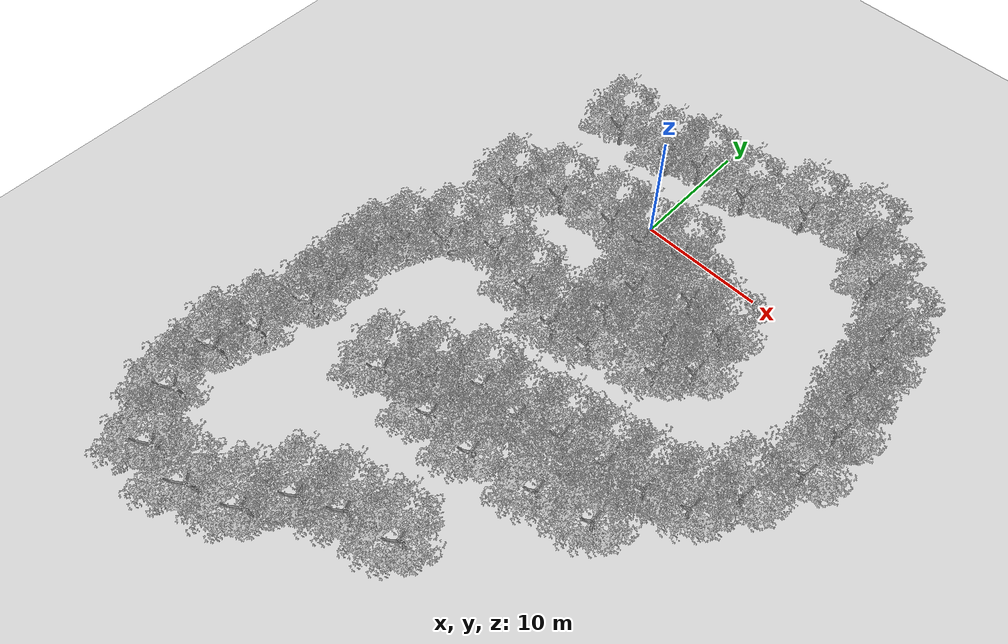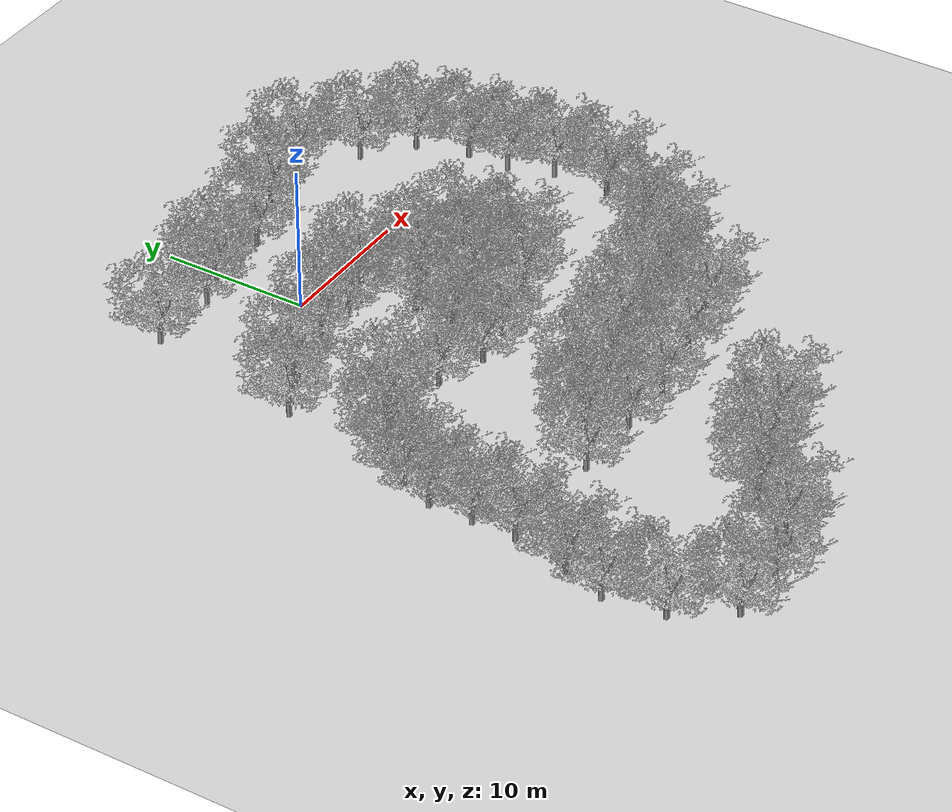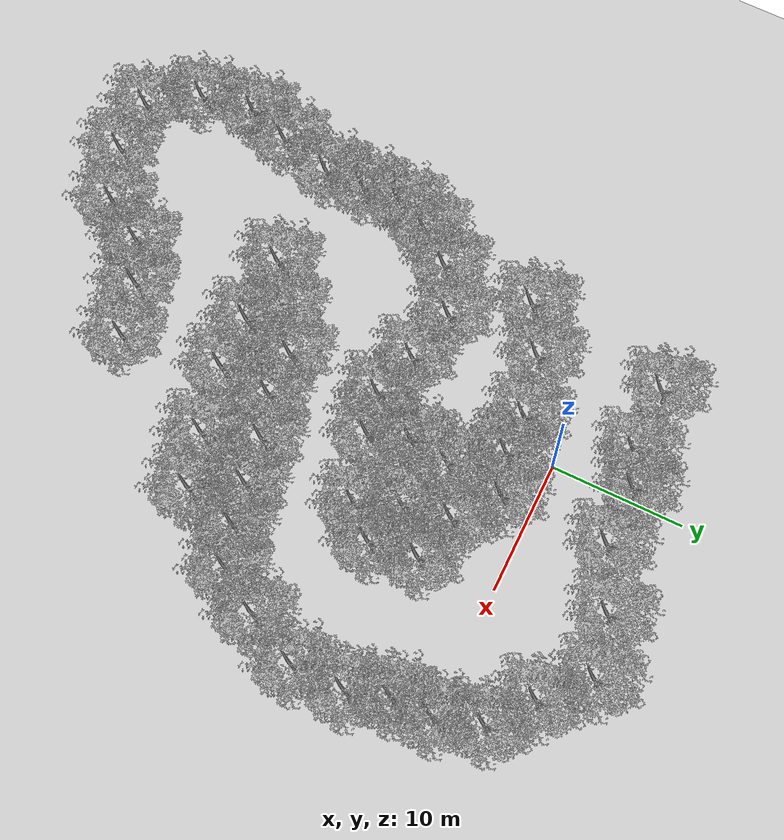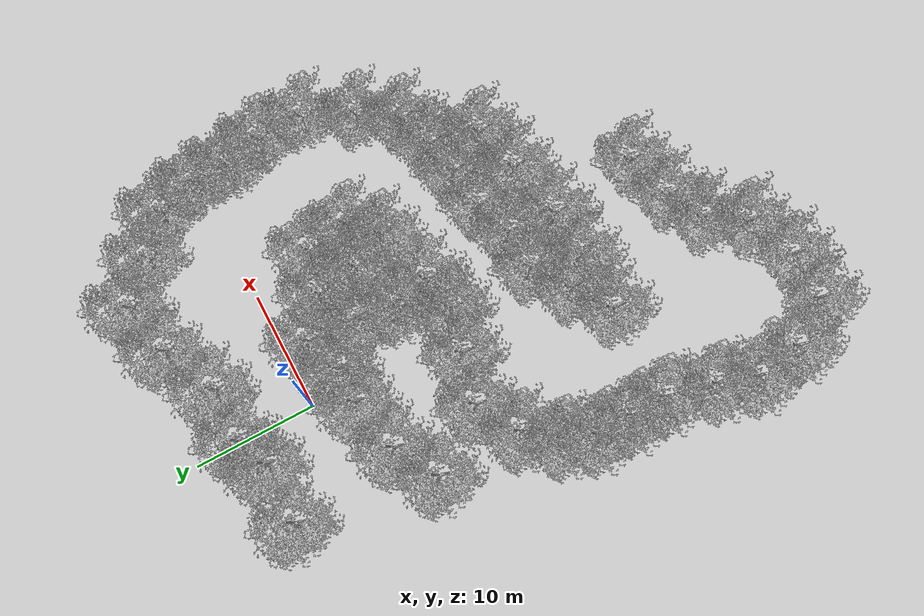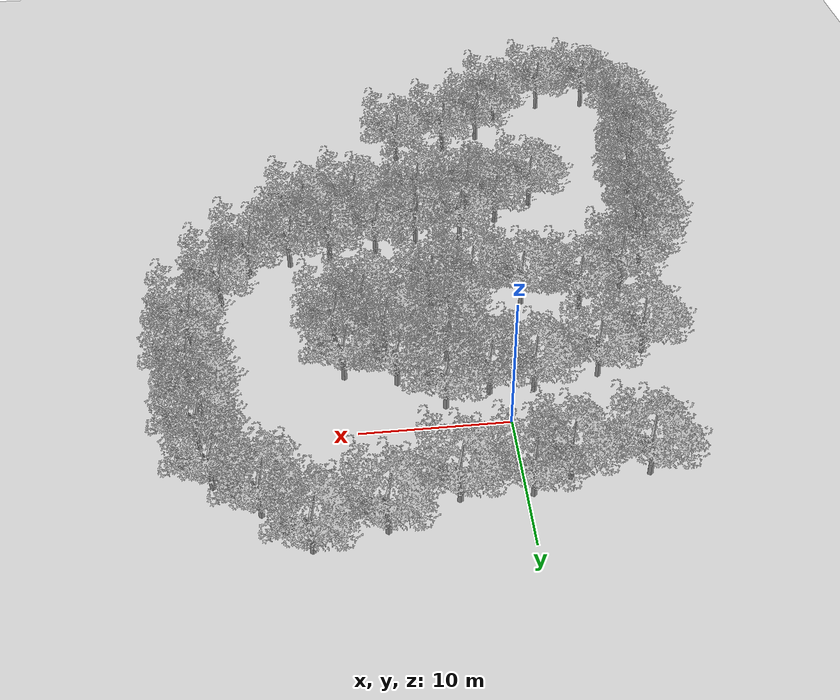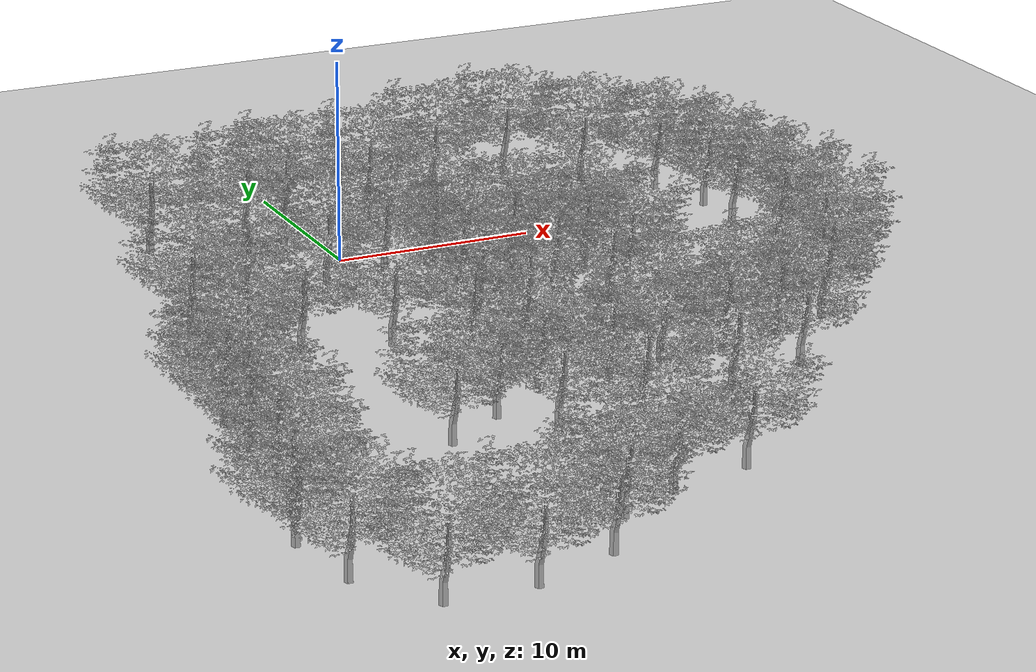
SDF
<?xml version="1.0" ?>
<gazebo version="1.2">
	<world name="default">

		<scene>
			<grid>false</grid>
		</scene>

    	<!-- A global light source -->
		<include>
			<uri>model://sun</uri>
		</include>

    	<!-- A ground plane -->
		<include>
			<uri>model://ground_plane</uri>
		</include>

		<model name='finihed'>
			<pose>8.508060 8.000000 0.000000 0.000000 -0.000000 0.000000</pose>
			<static>1</static>
			<allow_auto_disable>1</allow_auto_disable>
			<link name='link'>
				<pose>0.000000 0.000000 0.000000 0.000000 -0.000000 0.000000</pose>
				<inertial>
					<mass>10.000000</mass>
					<pose>0.000000 0.000000 0.000000 0.000000 -0.000000 0.000000</pose>
					<inertia>
						<ixx>0.001000</ixx>
						<ixy>0.000000</ixy>
						<ixz>0.000000</ixz>
						<iyy>0.001000</iyy>
						<iyz>0.000000</iyz>
						<izz>0.001000</izz>
					</inertia>
				</inertial>
				<collision name='collision'>
					<geometry>
						<cylinder>
							<radius>0.150000</radius>
							<length>5.000000</length>
						</cylinder>
					</geometry>
					<surface>
						<bounce />
						<friction>
							<ode />
						</friction>
						<contact>
							<ode />
						</contact>
					</surface>
				</collision>
				<visual name='visual'>
					<geometry>
						<mesh>
							<uri>model://finihed/meshes/finihed.dae</uri>
							<scale>1.000000 1.000000 1.000000</scale>
						</mesh>
					</geometry>
				</visual>
				<velocity_decay>
					<linear>0.000000</linear>
					<angular>0.000000</angular>
				</velocity_decay>
				<self_collide>0</self_collide>
				<kinematic>0</kinematic>
			</link>
		</model>

		<model name='finihed_0'>
			<pose>-0.515080 6.000000 0.000000 0.000000 -0.000000 0.000000</pose>
			<static>1</static>
			<allow_auto_disable>1</allow_auto_disable>
			<link name='link'>
				<pose>0.000000 0.000000 0.000000 0.000000 -0.000000 0.000000</pose>
				<inertial>
					<mass>10.000000</mass>
					<pose>0.000000 0.000000 0.000000 0.000000 -0.000000 0.000000</pose>
					<inertia>
						<ixx>0.001000</ixx>
						<ixy>0.000000</ixy>
						<ixz>0.000000</ixz>
						<iyy>0.001000</iyy>
						<iyz>0.000000</iyz>
						<izz>0.001000</izz>
					</inertia>
				</inertial>
				<collision name='collision'>
					<geometry>
						<cylinder>
							<radius>0.150000</radius>
							<length>5.000000</length>
						</cylinder>
					</geometry>
					<surface>
						<bounce />
						<friction>
							<ode />
						</friction>
						<contact>
							<ode />
						</contact>
					</surface>
				</collision>
				<visual name='visual'>
					<geometry>
						<mesh>
							<uri>model://finihed/meshes/finihed.dae</uri>
							<scale>1.000000 1.000000 1.000000</scale>
						</mesh>
					</geometry>
				</visual>
				<velocity_decay>
					<linear>0.000000</linear>
					<angular>0.000000</angular>
				</velocity_decay>
				<self_collide>0</self_collide>
				<kinematic>0</kinematic>
			</link>
		</model>
		<model name='finihed_1'>
			<pose>20.000000 0.000000 0.000000 0.000000 -0.000000 0.000000</pose>
			<static>1</static>
			<allow_auto_disable>1</allow_auto_disable>
			<link name='link'>
				<pose>0.000000 0.000000 0.000000 0.000000 -0.000000 0.000000</pose>
				<inertial>
					<mass>10.000000</mass>
					<pose>0.000000 0.000000 0.000000 0.000000 -0.000000 0.000000</pose>
					<inertia>
						<ixx>0.001000</ixx>
						<ixy>0.000000</ixy>
						<ixz>0.000000</ixz>
						<iyy>0.001000</iyy>
						<iyz>0.000000</iyz>
						<izz>0.001000</izz>
					</inertia>
				</inertial>
				<collision name='collision'>
					<geometry>
						<cylinder>
							<radius>0.150000</radius>
							<length>5.000000</length>
						</cylinder>
					</geometry>
					<surface>
						<bounce />
						<friction>
							<ode />
						</friction>
						<contact>
							<ode />
						</contact>
					</surface>
				</collision>
				<visual name='visual'>
					<geometry>
						<mesh>
							<uri>model://finihed/meshes/finihed.dae</uri>
							<scale>1.000000 1.000000 1.000000</scale>
						</mesh>
					</geometry>
				</visual>
				<velocity_decay>
					<linear>0.000000</linear>
					<angular>0.000000</angular>
				</velocity_decay>
				<self_collide>0</self_collide>
				<kinematic>0</kinematic>
			</link>
		</model>
		<model name='finihed_2'>
			<pose>16.000000 6.000000 0.000000 0.000000 -0.000000 0.000000</pose>
			<static>1</static>
			<allow_auto_disable>1</allow_auto_disable>
			<link name='link'>
				<pose>0.000000 0.000000 0.000000 0.000000 -0.000000 0.000000</pose>
				<inertial>
					<mass>10.000000</mass>
					<pose>0.000000 0.000000 0.000000 0.000000 -0.000000 0.000000</pose>
					<inertia>
						<ixx>0.001000</ixx>
						<ixy>0.000000</ixy>
						<ixz>0.000000</ixz>
						<iyy>0.001000</iyy>
						<iyz>0.000000</iyz>
						<izz>0.001000</izz>
					</inertia>
				</inertial>
				<collision name='collision'>
					<geometry>
						<cylinder>
							<radius>0.150000</radius>
							<length>5.000000</length>
						</cylinder>
					</geometry>
					<surface>
						<bounce />
						<friction>
							<ode />
						</friction>
						<contact>
							<ode />
						</contact>
					</surface>
				</collision>
				<visual name='visual'>
					<geometry>
						<mesh>
							<uri>model://finihed/meshes/finihed.dae</uri>
							<scale>1.000000 1.000000 1.000000</scale>
						</mesh>
					</geometry>
				</visual>
				<velocity_decay>
					<linear>0.000000</linear>
					<angular>0.000000</angular>
				</velocity_decay>
				<self_collide>0</self_collide>
				<kinematic>0</kinematic>
			</link>
		</model>
		<model name='finihed_3'>
			<pose>-8.000000 5.000000 0.000000 0.000000 -0.000000 0.000000</pose>
			<static>1</static>
			<allow_auto_disable>1</allow_auto_disable>
			<link name='link'>
				<pose>0.000000 0.000000 0.000000 0.000000 -0.000000 0.000000</pose>
				<inertial>
					<mass>10.000000</mass>
					<pose>0.000000 0.000000 0.000000 0.000000 -0.000000 0.000000</pose>
					<inertia>
						<ixx>0.001000</ixx>
						<ixy>0.000000</ixy>
						<ixz>0.000000</ixz>
						<iyy>0.001000</iyy>
						<iyz>0.000000</iyz>
						<izz>0.001000</izz>
					</inertia>
				</inertial>
				<collision name='collision'>
					<geometry>
						<cylinder>
							<radius>0.150000</radius>
							<length>5.000000</length>
						</cylinder>
					</geometry>
					<surface>
						<bounce />
						<friction>
							<ode />
						</friction>
						<contact>
							<ode />
						</contact>
					</surface>
				</collision>
				<visual name='visual'>
					<geometry>
						<mesh>
							<uri>model://finihed/meshes/finihed.dae</uri>
							<scale>1.000000 1.000000 1.000000</scale>
						</mesh>
					</geometry>
				</visual>
				<velocity_decay>
					<linear>0.000000</linear>
					<angular>0.000000</angular>
				</velocity_decay>
				<self_collide>0</self_collide>
				<kinematic>0</kinematic>
			</link>
		</model>
		<model name='finihed_4'>
			<pose>1.000000 -3.000000 0.000000 0.000000 -0.000000 0.000000</pose>
			<static>1</static>
			<allow_auto_disable>1</allow_auto_disable>
			<link name='link'>
				<pose>0.000000 0.000000 0.000000 0.000000 -0.000000 0.000000</pose>
				<inertial>
					<mass>10.000000</mass>
					<pose>0.000000 0.000000 0.000000 0.000000 -0.000000 0.000000</pose>
					<inertia>
						<ixx>0.001000</ixx>
						<ixy>0.000000</ixy>
						<ixz>0.000000</ixz>
						<iyy>0.001000</iyy>
						<iyz>0.000000</iyz>
						<izz>0.001000</izz>
					</inertia>
				</inertial>
				<collision name='collision'>
					<geometry>
						<cylinder>
							<radius>0.150000</radius>
							<length>5.000000</length>
						</cylinder>
					</geometry>
					<surface>
						<bounce />
						<friction>
							<ode />
						</friction>
						<contact>
							<ode />
						</contact>
					</surface>
				</collision>
				<visual name='visual'>
					<geometry>
						<mesh>
							<uri>model://finihed/meshes/finihed.dae</uri>
							<scale>1.000000 1.000000 1.000000</scale>
						</mesh>
					</geometry>
				</visual>
				<velocity_decay>
					<linear>0.000000</linear>
					<angular>0.000000</angular>
				</velocity_decay>
				<self_collide>0</self_collide>
				<kinematic>0</kinematic>
			</link>
		</model>
		<model name='finihed_5'>
			<pose>7.000000 -4.502550 0.000000 0.000000 -0.000000 0.000000</pose>
			<static>1</static>
			<allow_auto_disable>1</allow_auto_disable>
			<link name='link'>
				<pose>0.000000 0.000000 0.000000 0.000000 -0.000000 0.000000</pose>
				<inertial>
					<mass>10.000000</mass>
					<pose>0.000000 0.000000 0.000000 0.000000 -0.000000 0.000000</pose>
					<inertia>
						<ixx>0.001000</ixx>
						<ixy>0.000000</ixy>
						<ixz>0.000000</ixz>
						<iyy>0.001000</iyy>
						<iyz>0.000000</iyz>
						<izz>0.001000</izz>
					</inertia>
				</inertial>
				<collision name='collision'>
					<geometry>
						<cylinder>
							<radius>0.150000</radius>
							<length>5.000000</length>
						</cylinder>
					</geometry>
					<surface>
						<bounce />
						<friction>
							<ode />
						</friction>
						<contact>
							<ode />
						</contact>
					</surface>
				</collision>
				<visual name='visual'>
					<geometry>
						<mesh>
							<uri>model://finihed/meshes/finihed.dae</uri>
							<scale>1.000000 1.000000 1.000000</scale>
						</mesh>
					</geometry>
				</visual>
				<velocity_decay>
					<linear>0.000000</linear>
					<angular>0.000000</angular>
				</velocity_decay>
				<self_collide>0</self_collide>
				<kinematic>0</kinematic>
			</link>
		</model>
		<model name='finihed_6'>
			<pose>11.000000 -9.000000 0.000000 0.000000 -0.000000 0.000000</pose>
			<static>1</static>
			<allow_auto_disable>1</allow_auto_disable>
			<link name='link'>
				<pose>0.000000 0.000000 0.000000 0.000000 -0.000000 0.000000</pose>
				<inertial>
					<mass>10.000000</mass>
					<pose>0.000000 0.000000 0.000000 0.000000 -0.000000 0.000000</pose>
					<inertia>
						<ixx>0.001000</ixx>
						<ixy>0.000000</ixy>
						<ixz>0.000000</ixz>
						<iyy>0.001000</iyy>
						<iyz>0.000000</iyz>
						<izz>0.001000</izz>
					</inertia>
				</inertial>
				<collision name='collision'>
					<geometry>
						<cylinder>
							<radius>0.150000</radius>
							<length>5.000000</length>
						</cylinder>
					</geometry>
					<surface>
						<bounce />
						<friction>
							<ode />
						</friction>
						<contact>
							<ode />
						</contact>
					</surface>
				</collision>
				<visual name='visual'>
					<geometry>
						<mesh>
							<uri>model://finihed/meshes/finihed.dae</uri>
							<scale>1.000000 1.000000 1.000000</scale>
						</mesh>
					</geometry>
				</visual>
				<velocity_decay>
					<linear>0.000000</linear>
					<angular>0.000000</angular>
				</velocity_decay>
				<self_collide>0</self_collide>
				<kinematic>0</kinematic>
			</link>
		</model>
		<model name='finihed_7'>
			<pose>19.000000 3.502910 0.000000 0.000000 -0.000000 0.000000</pose>
			<static>1</static>
			<allow_auto_disable>1</allow_auto_disable>
			<link name='link'>
				<pose>0.000000 0.000000 0.000000 0.000000 -0.000000 0.000000</pose>
				<inertial>
					<mass>10.000000</mass>
					<pose>0.000000 0.000000 0.000000 0.000000 -0.000000 0.000000</pose>
					<inertia>
						<ixx>0.001000</ixx>
						<ixy>0.000000</ixy>
						<ixz>0.000000</ixz>
						<iyy>0.001000</iyy>
						<iyz>0.000000</iyz>
						<izz>0.001000</izz>
					</inertia>
				</inertial>
				<collision name='collision'>
					<geometry>
						<cylinder>
							<radius>0.150000</radius>
							<length>5.000000</length>
						</cylinder>
					</geometry>
					<surface>
						<bounce />
						<friction>
							<ode />
						</friction>
						<contact>
							<ode />
						</contact>
					</surface>
				</collision>
				<visual name='visual'>
					<geometry>
						<mesh>
							<uri>model://finihed/meshes/finihed.dae</uri>
							<scale>1.000000 1.000000 1.000000</scale>
						</mesh>
					</geometry>
				</visual>
				<velocity_decay>
					<linear>0.000000</linear>
					<angular>0.000000</angular>
				</velocity_decay>
				<self_collide>0</self_collide>
				<kinematic>0</kinematic>
			</link>
		</model>
		<model name='finihed_8'>
			<pose>13.000000 9.000000 0.000000 0.000000 -0.000000 0.000000</pose>
			<static>1</static>
			<allow_auto_disable>1</allow_auto_disable>
			<link name='link'>
				<pose>0.000000 0.000000 0.000000 0.000000 -0.000000 0.000000</pose>
				<inertial>
					<mass>10.000000</mass>
					<pose>0.000000 0.000000 0.000000 0.000000 -0.000000 0.000000</pose>
					<inertia>
						<ixx>0.001000</ixx>
						<ixy>0.000000</ixy>
						<ixz>0.000000</ixz>
						<iyy>0.001000</iyy>
						<iyz>0.000000</iyz>
						<izz>0.001000</izz>
					</inertia>
				</inertial>
				<collision name='collision'>
					<geometry>
						<cylinder>
							<radius>0.150000</radius>
							<length>5.000000</length>
						</cylinder>
					</geometry>
					<surface>
						<bounce />
						<friction>
							<ode />
						</friction>
						<contact>
							<ode />
						</contact>
					</surface>
				</collision>
				<visual name='visual'>
					<geometry>
						<mesh>
							<uri>model://finihed/meshes/finihed.dae</uri>
							<scale>1.000000 1.000000 1.000000</scale>
						</mesh>
					</geometry>
				</visual>
				<velocity_decay>
					<linear>0.000000</linear>
					<angular>0.000000</angular>
				</velocity_decay>
				<self_collide>0</self_collide>
				<kinematic>0</kinematic>
			</link>
		</model>
		<model name='finihed_9'>
			<pose>4.000000 6.000000 0.000000 0.000000 -0.000000 0.000000</pose>
			<static>1</static>
			<allow_auto_disable>1</allow_auto_disable>
			<link name='link'>
				<pose>0.000000 0.000000 0.000000 0.000000 -0.000000 0.000000</pose>
				<inertial>
					<mass>10.000000</mass>
					<pose>0.000000 0.000000 0.000000 0.000000 -0.000000 0.000000</pose>
					<inertia>
						<ixx>0.001000</ixx>
						<ixy>0.000000</ixy>
						<ixz>0.000000</ixz>
						<iyy>0.001000</iyy>
						<iyz>0.000000</iyz>
						<izz>0.001000</izz>
					</inertia>
				</inertial>
				<collision name='collision'>
					<geometry>
						<cylinder>
							<radius>0.150000</radius>
							<length>5.000000</length>
						</cylinder>
					</geometry>
					<surface>
						<bounce />
						<friction>
							<ode />
						</friction>
						<contact>
							<ode />
						</contact>
					</surface>
				</collision>
				<visual name='visual'>
					<geometry>
						<mesh>
							<uri>model://finihed/meshes/finihed.dae</uri>
							<scale>1.000000 1.000000 1.000000</scale>
						</mesh>
					</geometry>
				</visual>
				<velocity_decay>
					<linear>0.000000</linear>
					<angular>0.000000</angular>
				</velocity_decay>
				<self_collide>0</self_collide>
				<kinematic>0</kinematic>
			</link>
		</model>
		<model name='finihed_10'>
			<pose>4.000000 -2.000000 0.000000 0.000000 -0.000000 0.000000</pose>
			<static>1</static>
			<allow_auto_disable>1</allow_auto_disable>
			<link name='link'>
				<pose>0.000000 0.000000 0.000000 0.000000 -0.000000 0.000000</pose>
				<inertial>
					<mass>10.000000</mass>
					<pose>0.000000 0.000000 0.000000 0.000000 -0.000000 0.000000</pose>
					<inertia>
						<ixx>0.001000</ixx>
						<ixy>0.000000</ixy>
						<ixz>0.000000</ixz>
						<iyy>0.001000</iyy>
						<iyz>0.000000</iyz>
						<izz>0.001000</izz>
					</inertia>
				</inertial>
				<collision name='collision'>
					<geometry>
						<cylinder>
							<radius>0.150000</radius>
							<length>5.000000</length>
						</cylinder>
					</geometry>
					<surface>
						<bounce />
						<friction>
							<ode />
						</friction>
						<contact>
							<ode />
						</contact>
					</surface>
				</collision>
				<visual name='visual'>
					<geometry>
						<mesh>
							<uri>model://finihed/meshes/finihed.dae</uri>
							<scale>1.000000 1.000000 1.000000</scale>
						</mesh>
					</geometry>
				</visual>
				<velocity_decay>
					<linear>0.000000</linear>
					<angular>0.000000</angular>
				</velocity_decay>
				<self_collide>0</self_collide>
				<kinematic>0</kinematic>
			</link>
		</model>
		<model name='finihed_11'>
			<pose>10.517400 -5.416000 0.000000 0.000000 -0.000000 0.000000</pose>
			<static>1</static>
			<allow_auto_disable>1</allow_auto_disable>
			<link name='link'>
				<pose>0.000000 0.000000 0.000000 0.000000 -0.000000 0.000000</pose>
				<inertial>
					<mass>10.000000</mass>
					<pose>0.000000 0.000000 0.000000 0.000000 -0.000000 0.000000</pose>
					<inertia>
						<ixx>0.001000</ixx>
						<ixy>0.000000</ixy>
						<ixz>0.000000</ixz>
						<iyy>0.001000</iyy>
						<iyz>0.000000</iyz>
						<izz>0.001000</izz>
					</inertia>
				</inertial>
				<collision name='collision'>
					<geometry>
						<cylinder>
							<radius>0.150000</radius>
							<length>5.000000</length>
						</cylinder>
					</geometry>
					<surface>
						<bounce />
						<friction>
							<ode />
						</friction>
						<contact>
							<ode />
						</contact>
					</surface>
				</collision>
				<visual name='visual'>
					<geometry>
						<mesh>
							<uri>model://finihed/meshes/finihed.dae</uri>
							<scale>1.000000 1.000000 1.000000</scale>
						</mesh>
					</geometry>
				</visual>
				<velocity_decay>
					<linear>0.000000</linear>
					<angular>0.000000</angular>
				</velocity_decay>
				<self_collide>0</self_collide>
				<kinematic>0</kinematic>
			</link>
		</model>
		<model name='finihed_12'>
			<pose>20.000000 -3.000000 0.000000 0.000000 -0.000000 0.000000</pose>
			<static>1</static>
			<allow_auto_disable>1</allow_auto_disable>
			<link name='link'>
				<pose>0.000000 0.000000 0.000000 0.000000 -0.000000 0.000000</pose>
				<inertial>
					<mass>10.000000</mass>
					<pose>0.000000 0.000000 0.000000 0.000000 -0.000000 0.000000</pose>
					<inertia>
						<ixx>0.001000</ixx>
						<ixy>0.000000</ixy>
						<ixz>0.000000</ixz>
						<iyy>0.001000</iyy>
						<iyz>0.000000</iyz>
						<izz>0.001000</izz>
					</inertia>
				</inertial>
				<collision name='collision'>
					<geometry>
						<cylinder>
							<radius>0.150000</radius>
							<length>5.000000</length>
						</cylinder>
					</geometry>
					<surface>
						<bounce />
						<friction>
							<ode />
						</friction>
						<contact>
							<ode />
						</contact>
					</surface>
				</collision>
				<visual name='visual'>
					<geometry>
						<mesh>
							<uri>model://finihed/meshes/finihed.dae</uri>
							<scale>1.000000 1.000000 1.000000</scale>
						</mesh>
					</geometry>
				</visual>
				<velocity_decay>
					<linear>0.000000</linear>
					<angular>0.000000</angular>
				</velocity_decay>
				<self_collide>0</self_collide>
				<kinematic>0</kinematic>
			</link>
		</model>

		<model name='finihed_13'>
			<pose>21.000000 -6.000000 0.000000 0.000000 -0.000000 0.000000</pose>
			<static>1</static>
			<allow_auto_disable>1</allow_auto_disable>
			<link name='link'>
				<pose>0.000000 0.000000 0.000000 0.000000 -0.000000 0.000000</pose>
				<inertial>
					<mass>10.000000</mass>
					<pose>0.000000 0.000000 0.000000 0.000000 -0.000000 0.000000</pose>
					<inertia>
						<ixx>0.001000</ixx>
						<ixy>0.000000</ixy>
						<ixz>0.000000</ixz>
						<iyy>0.001000</iyy>
						<iyz>0.000000</iyz>
						<izz>0.001000</izz>
					</inertia>
				</inertial>
				<collision name='collision'>
					<geometry>
						<cylinder>
							<radius>0.150000</radius>
							<length>5.000000</length>
						</cylinder>
					</geometry>
					<surface>
						<bounce />
						<friction>
							<ode />
						</friction>
						<contact>
							<ode />
						</contact>
					</surface>
				</collision>
				<visual name='visual'>
					<geometry>
						<mesh>
							<uri>model://finihed/meshes/finihed.dae</uri>
							<scale>1.000000 1.000000 1.000000</scale>
						</mesh>
					</geometry>
				</visual>
				<velocity_decay>
					<linear>0.000000</linear>
					<angular>0.000000</angular>
				</velocity_decay>
				<self_collide>0</self_collide>
				<kinematic>0</kinematic>
			</link>
		</model>
		<model name='finihed_14'>
			<pose>21.000000 -10.000000 0.000000 0.000000 -0.000000 0.000000</pose>
			<static>1</static>
			<allow_auto_disable>1</allow_auto_disable>
			<link name='link'>
				<pose>0.000000 0.000000 0.000000 0.000000 -0.000000 0.000000</pose>
				<inertial>
					<mass>10.000000</mass>
					<pose>0.000000 0.000000 0.000000 0.000000 -0.000000 0.000000</pose>
					<inertia>
						<ixx>0.001000</ixx>
						<ixy>0.000000</ixy>
						<ixz>0.000000</ixz>
						<iyy>0.001000</iyy>
						<iyz>0.000000</iyz>
						<izz>0.001000</izz>
					</inertia>
				</inertial>
				<collision name='collision'>
					<geometry>
						<cylinder>
							<radius>0.150000</radius>
							<length>5.000000</length>
						</cylinder>
					</geometry>
					<surface>
						<bounce />
						<friction>
							<ode />
						</friction>
						<contact>
							<ode />
						</contact>
					</surface>
				</collision>
				<visual name='visual'>
					<geometry>
						<mesh>
							<uri>model://finihed/meshes/finihed.dae</uri>
							<scale>1.000000 1.000000 1.000000</scale>
						</mesh>
					</geometry>
				</visual>
				<velocity_decay>
					<linear>0.000000</linear>
					<angular>0.000000</angular>
				</velocity_decay>
				<self_collide>0</self_collide>
				<kinematic>0</kinematic>
			</link>
		</model>
		<model name='finihed_15'>
			<pose>19.000000 -14.000000 0.000000 0.000000 -0.000000 0.000000</pose>
			<static>1</static>
			<allow_auto_disable>1</allow_auto_disable>
			<link name='link'>
				<pose>0.000000 0.000000 0.000000 0.000000 -0.000000 0.000000</pose>
				<inertial>
					<mass>10.000000</mass>
					<pose>0.000000 0.000000 0.000000 0.000000 -0.000000 0.000000</pose>
					<inertia>
						<ixx>0.001000</ixx>
						<ixy>0.000000</ixy>
						<ixz>0.000000</ixz>
						<iyy>0.001000</iyy>
						<iyz>0.000000</iyz>
						<izz>0.001000</izz>
					</inertia>
				</inertial>
				<collision name='collision'>
					<geometry>
						<cylinder>
							<radius>0.150000</radius>
							<length>5.000000</length>
						</cylinder>
					</geometry>
					<surface>
						<bounce />
						<friction>
							<ode />
						</friction>
						<contact>
							<ode />
						</contact>
					</surface>
				</collision>
				<visual name='visual'>
					<geometry>
						<mesh>
							<uri>model://finihed/meshes/finihed.dae</uri>
							<scale>1.000000 1.000000 1.000000</scale>
						</mesh>
					</geometry>
				</visual>
				<velocity_decay>
					<linear>0.000000</linear>
					<angular>0.000000</angular>
				</velocity_decay>
				<self_collide>0</self_collide>
				<kinematic>0</kinematic>
			</link>
		</model>
		<model name='finihed_16'>
			<pose>17.000000 -17.000000 0.000000 0.000000 -0.000000 0.000000</pose>
			<static>1</static>
			<allow_auto_disable>1</allow_auto_disable>
			<link name='link'>
				<pose>0.000000 0.000000 0.000000 0.000000 -0.000000 0.000000</pose>
				<inertial>
					<mass>10.000000</mass>
					<pose>0.000000 0.000000 0.000000 0.000000 -0.000000 0.000000</pose>
					<inertia>
						<ixx>0.001000</ixx>
						<ixy>0.000000</ixy>
						<ixz>0.000000</ixz>
						<iyy>0.001000</iyy>
						<iyz>0.000000</iyz>
						<izz>0.001000</izz>
					</inertia>
				</inertial>
				<collision name='collision'>
					<geometry>
						<cylinder>
							<radius>0.150000</radius>
							<length>5.000000</length>
						</cylinder>
					</geometry>
					<surface>
						<bounce />
						<friction>
							<ode />
						</friction>
						<contact>
							<ode />
						</contact>
					</surface>
				</collision>
				<visual name='visual'>
					<geometry>
						<mesh>
							<uri>model://finihed/meshes/finihed.dae</uri>
							<scale>1.000000 1.000000 1.000000</scale>
						</mesh>
					</geometry>
				</visual>
				<velocity_decay>
					<linear>0.000000</linear>
					<angular>0.000000</angular>
				</velocity_decay>
				<self_collide>0</self_collide>
				<kinematic>0</kinematic>
			</link>
		</model>
		<model name='finihed_17'>
			<pose>14.000000 -18.000000 0.000000 0.000000 -0.000000 0.000000</pose>
			<static>1</static>
			<allow_auto_disable>1</allow_auto_disable>
			<link name='link'>
				<pose>0.000000 0.000000 0.000000 0.000000 -0.000000 0.000000</pose>
				<inertial>
					<mass>10.000000</mass>
					<pose>0.000000 0.000000 0.000000 0.000000 -0.000000 0.000000</pose>
					<inertia>
						<ixx>0.001000</ixx>
						<ixy>0.000000</ixy>
						<ixz>0.000000</ixz>
						<iyy>0.001000</iyy>
						<iyz>0.000000</iyz>
						<izz>0.001000</izz>
					</inertia>
				</inertial>
				<collision name='collision'>
					<geometry>
						<cylinder>
							<radius>0.150000</radius>
							<length>5.000000</length>
						</cylinder>
					</geometry>
					<surface>
						<bounce />
						<friction>
							<ode />
						</friction>
						<contact>
							<ode />
						</contact>
					</surface>
				</collision>
				<visual name='visual'>
					<geometry>
						<mesh>
							<uri>model://finihed/meshes/finihed.dae</uri>
							<scale>1.000000 1.000000 1.000000</scale>
						</mesh>
					</geometry>
				</visual>
				<velocity_decay>
					<linear>0.000000</linear>
					<angular>0.000000</angular>
				</velocity_decay>
				<self_collide>0</self_collide>
				<kinematic>0</kinematic>
			</link>
		</model>
		<model name='finihed_18'>
			<pose>9.000000 -11.000000 0.000000 0.000000 -0.000000 0.000000</pose>
			<static>1</static>
			<allow_auto_disable>1</allow_auto_disable>
			<link name='link'>
				<pose>0.000000 0.000000 0.000000 0.000000 -0.000000 0.000000</pose>
				<inertial>
					<mass>10.000000</mass>
					<pose>0.000000 0.000000 0.000000 0.000000 -0.000000 0.000000</pose>
					<inertia>
						<ixx>0.001000</ixx>
						<ixy>0.000000</ixy>
						<ixz>0.000000</ixz>
						<iyy>0.001000</iyy>
						<iyz>0.000000</iyz>
						<izz>0.001000</izz>
					</inertia>
				</inertial>
				<collision name='collision'>
					<geometry>
						<cylinder>
							<radius>0.150000</radius>
							<length>5.000000</length>
						</cylinder>
					</geometry>
					<surface>
						<bounce />
						<friction>
							<ode />
						</friction>
						<contact>
							<ode />
						</contact>
					</surface>
				</collision>
				<visual name='visual'>
					<geometry>
						<mesh>
							<uri>model://finihed/meshes/finihed.dae</uri>
							<scale>1.000000 1.000000 1.000000</scale>
						</mesh>
					</geometry>
				</visual>
				<velocity_decay>
					<linear>0.000000</linear>
					<angular>0.000000</angular>
				</velocity_decay>
				<self_collide>0</self_collide>
				<kinematic>0</kinematic>
			</link>
		</model>
		<model name='finihed_19'>
			<pose>4.000000 -12.426700 0.000000 0.000000 -0.000000 0.000000</pose>
			<static>1</static>
			<allow_auto_disable>1</allow_auto_disable>
			<link name='link'>
				<pose>0.000000 0.000000 0.000000 0.000000 -0.000000 0.000000</pose>
				<inertial>
					<mass>10.000000</mass>
					<pose>0.000000 0.000000 0.000000 0.000000 -0.000000 0.000000</pose>
					<inertia>
						<ixx>0.001000</ixx>
						<ixy>0.000000</ixy>
						<ixz>0.000000</ixz>
						<iyy>0.001000</iyy>
						<iyz>0.000000</iyz>
						<izz>0.001000</izz>
					</inertia>
				</inertial>
				<collision name='collision'>
					<geometry>
						<cylinder>
							<radius>0.150000</radius>
							<length>5.000000</length>
						</cylinder>
					</geometry>
					<surface>
						<bounce />
						<friction>
							<ode />
						</friction>
						<contact>
							<ode />
						</contact>
					</surface>
				</collision>
				<visual name='visual'>
					<geometry>
						<mesh>
							<uri>model://finihed/meshes/finihed.dae</uri>
							<scale>1.000000 1.000000 1.000000</scale>
						</mesh>
					</geometry>
				</visual>
				<velocity_decay>
					<linear>0.000000</linear>
					<angular>0.000000</angular>
				</velocity_decay>
				<self_collide>0</self_collide>
				<kinematic>0</kinematic>
			</link>
		</model>
		<model name='finihed_20'>
			<pose>1.000000 -13.000000 0.000000 0.000000 -0.000000 0.000000</pose>
			<static>1</static>
			<allow_auto_disable>1</allow_auto_disable>
			<link name='link'>
				<pose>0.000000 0.000000 0.000000 0.000000 -0.000000 0.000000</pose>
				<inertial>
					<mass>10.000000</mass>
					<pose>0.000000 0.000000 0.000000 0.000000 -0.000000 0.000000</pose>
					<inertia>
						<ixx>0.001000</ixx>
						<ixy>0.000000</ixy>
						<ixz>0.000000</ixz>
						<iyy>0.001000</iyy>
						<iyz>0.000000</iyz>
						<izz>0.001000</izz>
					</inertia>
				</inertial>
				<collision name='collision'>
					<geometry>
						<cylinder>
							<radius>0.150000</radius>
							<length>5.000000</length>
						</cylinder>
					</geometry>
					<surface>
						<bounce />
						<friction>
							<ode />
						</friction>
						<contact>
							<ode />
						</contact>
					</surface>
				</collision>
				<visual name='visual'>
					<geometry>
						<mesh>
							<uri>model://finihed/meshes/finihed.dae</uri>
							<scale>1.000000 1.000000 1.000000</scale>
						</mesh>
					</geometry>
				</visual>
				<velocity_decay>
					<linear>0.000000</linear>
					<angular>0.000000</angular>
				</velocity_decay>
				<self_collide>0</self_collide>
				<kinematic>0</kinematic>
			</link>
		</model>
		<model name='finihed_21'>
			<pose>11.000000 -18.522200 0.000000 0.000000 -0.000000 0.000000</pose>
			<static>1</static>
			<allow_auto_disable>1</allow_auto_disable>
			<link name='link'>
				<pose>0.000000 0.000000 0.000000 0.000000 -0.000000 0.000000</pose>
				<inertial>
					<mass>10.000000</mass>
					<pose>0.000000 0.000000 0.000000 0.000000 -0.000000 0.000000</pose>
					<inertia>
						<ixx>0.001000</ixx>
						<ixy>0.000000</ixy>
						<ixz>0.000000</ixz>
						<iyy>0.001000</iyy>
						<iyz>0.000000</iyz>
						<izz>0.001000</izz>
					</inertia>
				</inertial>
				<collision name='collision'>
					<geometry>
						<cylinder>
							<radius>0.150000</radius>
							<length>5.000000</length>
						</cylinder>
					</geometry>
					<surface>
						<bounce />
						<friction>
							<ode />
						</friction>
						<contact>
							<ode />
						</contact>
					</surface>
				</collision>
				<visual name='visual'>
					<geometry>
						<mesh>
							<uri>model://finihed/meshes/finihed.dae</uri>
							<scale>1.000000 1.000000 1.000000</scale>
						</mesh>
					</geometry>
				</visual>
				<velocity_decay>
					<linear>0.000000</linear>
					<angular>0.000000</angular>
				</velocity_decay>
				<self_collide>0</self_collide>
				<kinematic>0</kinematic>
			</link>
		</model>
		<model name='finihed_22'>
			<pose>7.524440 -19.000000 0.000000 0.000000 -0.000000 0.000000</pose>
			<static>1</static>
			<allow_auto_disable>1</allow_auto_disable>
			<link name='link'>
				<pose>0.000000 0.000000 0.000000 0.000000 -0.000000 0.000000</pose>
				<inertial>
					<mass>10.000000</mass>
					<pose>0.000000 0.000000 0.000000 0.000000 -0.000000 0.000000</pose>
					<inertia>
						<ixx>0.001000</ixx>
						<ixy>0.000000</ixy>
						<ixz>0.000000</ixz>
						<iyy>0.001000</iyy>
						<iyz>0.000000</iyz>
						<izz>0.001000</izz>
					</inertia>
				</inertial>
				<collision name='collision'>
					<geometry>
						<cylinder>
							<radius>0.150000</radius>
							<length>5.000000</length>
						</cylinder>
					</geometry>
					<surface>
						<bounce />
						<friction>
							<ode />
						</friction>
						<contact>
							<ode />
						</contact>
					</surface>
				</collision>
				<visual name='visual'>
					<geometry>
						<mesh>
							<uri>model://finihed/meshes/finihed.dae</uri>
							<scale>1.000000 1.000000 1.000000</scale>
						</mesh>
					</geometry>
				</visual>
				<velocity_decay>
					<linear>0.000000</linear>
					<angular>0.000000</angular>
				</velocity_decay>
				<self_collide>0</self_collide>
				<kinematic>0</kinematic>
			</link>
		</model>
		<model name='finihed_23'>
			<pose>4.400020 -20.000000 0.000000 0.000000 -0.000000 0.000000</pose>
			<static>1</static>
			<allow_auto_disable>1</allow_auto_disable>
			<link name='link'>
				<pose>0.000000 0.000000 0.000000 0.000000 -0.000000 0.000000</pose>
				<inertial>
					<mass>10.000000</mass>
					<pose>0.000000 0.000000 0.000000 0.000000 -0.000000 0.000000</pose>
					<inertia>
						<ixx>0.001000</ixx>
						<ixy>0.000000</ixy>
						<ixz>0.000000</ixz>
						<iyy>0.001000</iyy>
						<iyz>0.000000</iyz>
						<izz>0.001000</izz>
					</inertia>
				</inertial>
				<collision name='collision'>
					<geometry>
						<cylinder>
							<radius>0.150000</radius>
							<length>5.000000</length>
						</cylinder>
					</geometry>
					<surface>
						<bounce />
						<friction>
							<ode />
						</friction>
						<contact>
							<ode />
						</contact>
					</surface>
				</collision>
				<visual name='visual'>
					<geometry>
						<mesh>
							<uri>model://finihed/meshes/finihed.dae</uri>
							<scale>1.000000 1.000000 1.000000</scale>
						</mesh>
					</geometry>
				</visual>
				<velocity_decay>
					<linear>0.000000</linear>
					<angular>0.000000</angular>
				</velocity_decay>
				<self_collide>0</self_collide>
				<kinematic>0</kinematic>
			</link>
		</model>
		<model name='finihed_24'>
			<pose>1.000000 -20.000000 0.000000 0.000000 -0.000000 0.000000</pose>
			<static>1</static>
			<allow_auto_disable>1</allow_auto_disable>
			<link name='link'>
				<pose>0.000000 0.000000 0.000000 0.000000 -0.000000 0.000000</pose>
				<inertial>
					<mass>10.000000</mass>
					<pose>0.000000 0.000000 0.000000 0.000000 -0.000000 0.000000</pose>
					<inertia>
						<ixx>0.001000</ixx>
						<ixy>0.000000</ixy>
						<ixz>0.000000</ixz>
						<iyy>0.001000</iyy>
						<iyz>0.000000</iyz>
						<izz>0.001000</izz>
					</inertia>
				</inertial>
				<collision name='collision'>
					<geometry>
						<cylinder>
							<radius>0.150000</radius>
							<length>5.000000</length>
						</cylinder>
					</geometry>
					<surface>
						<bounce />
						<friction>
							<ode />
						</friction>
						<contact>
							<ode />
						</contact>
					</surface>
				</collision>
				<visual name='visual'>
					<geometry>
						<mesh>
							<uri>model://finihed/meshes/finihed.dae</uri>
							<scale>1.000000 1.000000 1.000000</scale>
						</mesh>
					</geometry>
				</visual>
				<velocity_decay>
					<linear>0.000000</linear>
					<angular>0.000000</angular>
				</velocity_decay>
				<self_collide>0</self_collide>
				<kinematic>0</kinematic>
			</link>
		</model>
		<model name='finihed_25'>
			<pose>7.596890 -8.000000 0.000000 0.000000 -0.000000 0.000000</pose>
			<static>1</static>
			<allow_auto_disable>1</allow_auto_disable>
			<link name='link'>
				<pose>0.000000 0.000000 0.000000 0.000000 -0.000000 0.000000</pose>
				<inertial>
					<mass>10.000000</mass>
					<pose>0.000000 0.000000 0.000000 0.000000 -0.000000 0.000000</pose>
					<inertia>
						<ixx>0.001000</ixx>
						<ixy>0.000000</ixy>
						<ixz>0.000000</ixz>
						<iyy>0.001000</iyy>
						<iyz>0.000000</iyz>
						<izz>0.001000</izz>
					</inertia>
				</inertial>
				<collision name='collision'>
					<geometry>
						<cylinder>
							<radius>0.150000</radius>
							<length>5.000000</length>
						</cylinder>
					</geometry>
					<surface>
						<bounce />
						<friction>
							<ode />
						</friction>
						<contact>
							<ode />
						</contact>
					</surface>
				</collision>
				<visual name='visual'>
					<geometry>
						<mesh>
							<uri>model://finihed/meshes/finihed.dae</uri>
							<scale>1.000000 1.000000 1.000000</scale>
						</mesh>
					</geometry>
				</visual>
				<velocity_decay>
					<linear>0.000000</linear>
					<angular>0.000000</angular>
				</velocity_decay>
				<self_collide>0</self_collide>
				<kinematic>0</kinematic>
			</link>
		</model>
		<model name='finihed_26'>
			<pose>3.431210 -6.503010 0.000000 0.000000 -0.000000 0.000000</pose>
			<static>1</static>
			<allow_auto_disable>1</allow_auto_disable>
			<link name='link'>
				<pose>0.000000 0.000000 0.000000 0.000000 -0.000000 0.000000</pose>
				<inertial>
					<mass>10.000000</mass>
					<pose>0.000000 0.000000 0.000000 0.000000 -0.000000 0.000000</pose>
					<inertia>
						<ixx>0.001000</ixx>
						<ixy>0.000000</ixy>
						<ixz>0.000000</ixz>
						<iyy>0.001000</iyy>
						<iyz>0.000000</iyz>
						<izz>0.001000</izz>
					</inertia>
				</inertial>
				<collision name='collision'>
					<geometry>
						<cylinder>
							<radius>0.150000</radius>
							<length>5.000000</length>
						</cylinder>
					</geometry>
					<surface>
						<bounce />
						<friction>
							<ode />
						</friction>
						<contact>
							<ode />
						</contact>
					</surface>
				</collision>
				<visual name='visual'>
					<geometry>
						<mesh>
							<uri>model://finihed/meshes/finihed.dae</uri>
							<scale>1.000000 1.000000 1.000000</scale>
						</mesh>
					</geometry>
				</visual>
				<velocity_decay>
					<linear>0.000000</linear>
					<angular>0.000000</angular>
				</velocity_decay>
				<self_collide>0</self_collide>
				<kinematic>0</kinematic>
			</link>
		</model>
		<model name='finihed_27'>
			<pose>3.000000 -9.525420 0.000000 0.000000 -0.000000 0.000000</pose>
			<static>1</static>
			<allow_auto_disable>1</allow_auto_disable>
			<link name='link'>
				<pose>0.000000 0.000000 0.000000 0.000000 -0.000000 0.000000</pose>
				<inertial>
					<mass>10.000000</mass>
					<pose>0.000000 0.000000 0.000000 0.000000 -0.000000 0.000000</pose>
					<inertia>
						<ixx>0.001000</ixx>
						<ixy>0.000000</ixy>
						<ixz>0.000000</ixz>
						<iyy>0.001000</iyy>
						<iyz>0.000000</iyz>
						<izz>0.001000</izz>
					</inertia>
				</inertial>
				<collision name='collision'>
					<geometry>
						<cylinder>
							<radius>0.150000</radius>
							<length>5.000000</length>
						</cylinder>
					</geometry>
					<surface>
						<bounce />
						<friction>
							<ode />
						</friction>
						<contact>
							<ode />
						</contact>
					</surface>
				</collision>
				<visual name='visual'>
					<geometry>
						<mesh>
							<uri>model://finihed/meshes/finihed.dae</uri>
							<scale>1.000000 1.000000 1.000000</scale>
						</mesh>
					</geometry>
				</visual>
				<velocity_decay>
					<linear>0.000000</linear>
					<angular>0.000000</angular>
				</velocity_decay>
				<self_collide>0</self_collide>
				<kinematic>0</kinematic>
			</link>
		</model>
		<model name='finihed_28'>
			<pose>-3.000000 5.000000 0.000000 0.000000 -0.000000 0.000000</pose>
			<static>1</static>
			<allow_auto_disable>1</allow_auto_disable>
			<link name='link'>
				<pose>0.000000 0.000000 0.000000 0.000000 -0.000000 0.000000</pose>
				<inertial>
					<mass>10.000000</mass>
					<pose>0.000000 0.000000 0.000000 0.000000 -0.000000 0.000000</pose>
					<inertia>
						<ixx>0.001000</ixx>
						<ixy>0.000000</ixy>
						<ixz>0.000000</ixz>
						<iyy>0.001000</iyy>
						<iyz>0.000000</iyz>
						<izz>0.001000</izz>
					</inertia>
				</inertial>
				<collision name='collision'>
					<geometry>
						<cylinder>
							<radius>0.150000</radius>
							<length>5.000000</length>
						</cylinder>
					</geometry>
					<surface>
						<bounce />
						<friction>
							<ode />
						</friction>
						<contact>
							<ode />
						</contact>
					</surface>
				</collision>
				<visual name='visual'>
					<geometry>
						<mesh>
							<uri>model://finihed/meshes/finihed.dae</uri>
							<scale>1.000000 1.000000 1.000000</scale>
						</mesh>
					</geometry>
				</visual>
				<velocity_decay>
					<linear>0.000000</linear>
					<angular>0.000000</angular>
				</velocity_decay>
				<self_collide>0</self_collide>
				<kinematic>0</kinematic>
			</link>
		</model>
		<model name='finihed_29'>
			<pose>-2.522530 -12.000000 0.000000 0.000000 -0.000000 0.000000</pose>
			<static>1</static>
			<allow_auto_disable>1</allow_auto_disable>
			<link name='link'>
				<pose>0.000000 0.000000 0.000000 0.000000 -0.000000 0.000000</pose>
				<inertial>
					<mass>10.000000</mass>
					<pose>0.000000 0.000000 0.000000 0.000000 -0.000000 0.000000</pose>
					<inertia>
						<ixx>0.001000</ixx>
						<ixy>0.000000</ixy>
						<ixz>0.000000</ixz>
						<iyy>0.001000</iyy>
						<iyz>0.000000</iyz>
						<izz>0.001000</izz>
					</inertia>
				</inertial>
				<collision name='collision'>
					<geometry>
						<cylinder>
							<radius>0.150000</radius>
							<length>5.000000</length>
						</cylinder>
					</geometry>
					<surface>
						<bounce />
						<friction>
							<ode />
						</friction>
						<contact>
							<ode />
						</contact>
					</surface>
				</collision>
				<visual name='visual'>
					<geometry>
						<mesh>
							<uri>model://finihed/meshes/finihed.dae</uri>
							<scale>1.000000 1.000000 1.000000</scale>
						</mesh>
					</geometry>
				</visual>
				<velocity_decay>
					<linear>0.000000</linear>
					<angular>0.000000</angular>
				</velocity_decay>
				<self_collide>0</self_collide>
				<kinematic>0</kinematic>
			</link>
		</model>
		<model name='finihed_30'>
			<pose>-6.565320 -11.000000 0.000000 0.000000 -0.000000 0.000000</pose>
			<static>1</static>
			<allow_auto_disable>1</allow_auto_disable>
			<link name='link'>
				<pose>0.000000 0.000000 0.000000 0.000000 -0.000000 0.000000</pose>
				<inertial>
					<mass>10.000000</mass>
					<pose>0.000000 0.000000 0.000000 0.000000 -0.000000 0.000000</pose>
					<inertia>
						<ixx>0.001000</ixx>
						<ixy>0.000000</ixy>
						<ixz>0.000000</ixz>
						<iyy>0.001000</iyy>
						<iyz>0.000000</iyz>
						<izz>0.001000</izz>
					</inertia>
				</inertial>
				<collision name='collision'>
					<geometry>
						<cylinder>
							<radius>0.150000</radius>
							<length>5.000000</length>
						</cylinder>
					</geometry>
					<surface>
						<bounce />
						<friction>
							<ode />
						</friction>
						<contact>
							<ode />
						</contact>
					</surface>
				</collision>
				<visual name='visual'>
					<geometry>
						<mesh>
							<uri>model://finihed/meshes/finihed.dae</uri>
							<scale>1.000000 1.000000 1.000000</scale>
						</mesh>
					</geometry>
				</visual>
				<velocity_decay>
					<linear>0.000000</linear>
					<angular>0.000000</angular>
				</velocity_decay>
				<self_collide>0</self_collide>
				<kinematic>0</kinematic>
			</link>
		</model>
		<model name='finihed_31'>
			<pose>-10.000000 -13.000000 0.000000 0.000000 -0.000000 0.000000</pose>
			<static>1</static>
			<allow_auto_disable>1</allow_auto_disable>
			<link name='link'>
				<pose>0.000000 0.000000 0.000000 0.000000 -0.000000 0.000000</pose>
				<inertial>
					<mass>10.000000</mass>
					<pose>0.000000 0.000000 0.000000 0.000000 -0.000000 0.000000</pose>
					<inertia>
						<ixx>0.001000</ixx>
						<ixy>0.000000</ixy>
						<ixz>0.000000</ixz>
						<iyy>0.001000</iyy>
						<iyz>0.000000</iyz>
						<izz>0.001000</izz>
					</inertia>
				</inertial>
				<collision name='collision'>
					<geometry>
						<cylinder>
							<radius>0.150000</radius>
							<length>5.000000</length>
						</cylinder>
					</geometry>
					<surface>
						<bounce />
						<friction>
							<ode />
						</friction>
						<contact>
							<ode />
						</contact>
					</surface>
				</collision>
				<visual name='visual'>
					<geometry>
						<mesh>
							<uri>model://finihed/meshes/finihed.dae</uri>
							<scale>1.000000 1.000000 1.000000</scale>
						</mesh>
					</geometry>
				</visual>
				<velocity_decay>
					<linear>0.000000</linear>
					<angular>0.000000</angular>
				</velocity_decay>
				<self_collide>0</self_collide>
				<kinematic>0</kinematic>
			</link>
		</model>
		<model name='finihed_32'>
			<pose>-12.000000 -15.574100 0.000000 0.000000 -0.000000 0.000000</pose>
			<static>1</static>
			<allow_auto_disable>1</allow_auto_disable>
			<link name='link'>
				<pose>0.000000 0.000000 0.000000 0.000000 -0.000000 0.000000</pose>
				<inertial>
					<mass>10.000000</mass>
					<pose>0.000000 0.000000 0.000000 0.000000 -0.000000 0.000000</pose>
					<inertia>
						<ixx>0.001000</ixx>
						<ixy>0.000000</ixy>
						<ixz>0.000000</ixz>
						<iyy>0.001000</iyy>
						<iyz>0.000000</iyz>
						<izz>0.001000</izz>
					</inertia>
				</inertial>
				<collision name='collision'>
					<geometry>
						<cylinder>
							<radius>0.150000</radius>
							<length>5.000000</length>
						</cylinder>
					</geometry>
					<surface>
						<bounce />
						<friction>
							<ode />
						</friction>
						<contact>
							<ode />
						</contact>
					</surface>
				</collision>
				<visual name='visual'>
					<geometry>
						<mesh>
							<uri>model://finihed/meshes/finihed.dae</uri>
							<scale>1.000000 1.000000 1.000000</scale>
						</mesh>
					</geometry>
				</visual>
				<velocity_decay>
					<linear>0.000000</linear>
					<angular>0.000000</angular>
				</velocity_decay>
				<self_collide>0</self_collide>
				<kinematic>0</kinematic>
			</link>
		</model>
		<model name='finihed_33'>
			<pose>-13.000000 -18.000000 0.000000 0.000000 -0.000000 0.000000</pose>
			<static>1</static>
			<allow_auto_disable>1</allow_auto_disable>
			<link name='link'>
				<pose>0.000000 0.000000 0.000000 0.000000 -0.000000 0.000000</pose>
				<inertial>
					<mass>10.000000</mass>
					<pose>0.000000 0.000000 0.000000 0.000000 -0.000000 0.000000</pose>
					<inertia>
						<ixx>0.001000</ixx>
						<ixy>0.000000</ixy>
						<ixz>0.000000</ixz>
						<iyy>0.001000</iyy>
						<iyz>0.000000</iyz>
						<izz>0.001000</izz>
					</inertia>
				</inertial>
				<collision name='collision'>
					<geometry>
						<cylinder>
							<radius>0.150000</radius>
							<length>5.000000</length>
						</cylinder>
					</geometry>
					<surface>
						<bounce />
						<friction>
							<ode />
						</friction>
						<contact>
							<ode />
						</contact>
					</surface>
				</collision>
				<visual name='visual'>
					<geometry>
						<mesh>
							<uri>model://finihed/meshes/finihed.dae</uri>
							<scale>1.000000 1.000000 1.000000</scale>
						</mesh>
					</geometry>
				</visual>
				<velocity_decay>
					<linear>0.000000</linear>
					<angular>0.000000</angular>
				</velocity_decay>
				<self_collide>0</self_collide>
				<kinematic>0</kinematic>
			</link>
		</model>
		<model name='finihed_34'>
			<pose>-13.000000 -21.000000 0.000000 0.000000 -0.000000 0.000000</pose>
			<static>1</static>
			<allow_auto_disable>1</allow_auto_disable>
			<link name='link'>
				<pose>0.000000 0.000000 0.000000 0.000000 -0.000000 0.000000</pose>
				<inertial>
					<mass>10.000000</mass>
					<pose>0.000000 0.000000 0.000000 0.000000 -0.000000 0.000000</pose>
					<inertia>
						<ixx>0.001000</ixx>
						<ixy>0.000000</ixy>
						<ixz>0.000000</ixz>
						<iyy>0.001000</iyy>
						<iyz>0.000000</iyz>
						<izz>0.001000</izz>
					</inertia>
				</inertial>
				<collision name='collision'>
					<geometry>
						<cylinder>
							<radius>0.150000</radius>
							<length>5.000000</length>
						</cylinder>
					</geometry>
					<surface>
						<bounce />
						<friction>
							<ode />
						</friction>
						<contact>
							<ode />
						</contact>
					</surface>
				</collision>
				<visual name='visual'>
					<geometry>
						<mesh>
							<uri>model://finihed/meshes/finihed.dae</uri>
							<scale>1.000000 1.000000 1.000000</scale>
						</mesh>
					</geometry>
				</visual>
				<velocity_decay>
					<linear>0.000000</linear>
					<angular>0.000000</angular>
				</velocity_decay>
				<self_collide>0</self_collide>
				<kinematic>0</kinematic>
			</link>
		</model>
		<model name='finihed_35'>
			<pose>-2.000000 -22.000000 0.000000 0.000000 -0.000000 0.000000</pose>
			<static>1</static>
			<allow_auto_disable>1</allow_auto_disable>
			<link name='link'>
				<pose>0.000000 0.000000 0.000000 0.000000 -0.000000 0.000000</pose>
				<inertial>
					<mass>10.000000</mass>
					<pose>0.000000 0.000000 0.000000 0.000000 -0.000000 0.000000</pose>
					<inertia>
						<ixx>0.001000</ixx>
						<ixy>0.000000</ixy>
						<ixz>0.000000</ixz>
						<iyy>0.001000</iyy>
						<iyz>0.000000</iyz>
						<izz>0.001000</izz>
					</inertia>
				</inertial>
				<collision name='collision'>
					<geometry>
						<cylinder>
							<radius>0.150000</radius>
							<length>5.000000</length>
						</cylinder>
					</geometry>
					<surface>
						<bounce />
						<friction>
							<ode />
						</friction>
						<contact>
							<ode />
						</contact>
					</surface>
				</collision>
				<visual name='visual'>
					<geometry>
						<mesh>
							<uri>model://finihed/meshes/finihed.dae</uri>
							<scale>1.000000 1.000000 1.000000</scale>
						</mesh>
					</geometry>
				</visual>
				<velocity_decay>
					<linear>0.000000</linear>
					<angular>0.000000</angular>
				</velocity_decay>
				<self_collide>0</self_collide>
				<kinematic>0</kinematic>
			</link>
		</model>
		<model name='finihed_36'>
			<pose>-5.000000 -24.000000 0.000000 0.000000 -0.000000 0.000000</pose>
			<static>1</static>
			<allow_auto_disable>1</allow_auto_disable>
			<link name='link'>
				<pose>0.000000 0.000000 0.000000 0.000000 -0.000000 0.000000</pose>
				<inertial>
					<mass>10.000000</mass>
					<pose>0.000000 0.000000 0.000000 0.000000 -0.000000 0.000000</pose>
					<inertia>
						<ixx>0.001000</ixx>
						<ixy>0.000000</ixy>
						<ixz>0.000000</ixz>
						<iyy>0.001000</iyy>
						<iyz>0.000000</iyz>
						<izz>0.001000</izz>
					</inertia>
				</inertial>
				<collision name='collision'>
					<geometry>
						<cylinder>
							<radius>0.150000</radius>
							<length>5.000000</length>
						</cylinder>
					</geometry>
					<surface>
						<bounce />
						<friction>
							<ode />
						</friction>
						<contact>
							<ode />
						</contact>
					</surface>
				</collision>
				<visual name='visual'>
					<geometry>
						<mesh>
							<uri>model://finihed/meshes/finihed.dae</uri>
							<scale>1.000000 1.000000 1.000000</scale>
						</mesh>
					</geometry>
				</visual>
				<velocity_decay>
					<linear>0.000000</linear>
					<angular>0.000000</angular>
				</velocity_decay>
				<self_collide>0</self_collide>
				<kinematic>0</kinematic>
			</link>
		</model>
		<model name='finihed_37'>
			<pose>-13.000000 -24.000000 0.000000 0.000000 -0.000000 0.000000</pose>
			<static>1</static>
			<allow_auto_disable>1</allow_auto_disable>
			<link name='link'>
				<pose>0.000000 0.000000 0.000000 0.000000 -0.000000 0.000000</pose>
				<inertial>
					<mass>10.000000</mass>
					<pose>0.000000 0.000000 0.000000 0.000000 -0.000000 0.000000</pose>
					<inertia>
						<ixx>0.001000</ixx>
						<ixy>0.000000</ixy>
						<ixz>0.000000</ixz>
						<iyy>0.001000</iyy>
						<iyz>0.000000</iyz>
						<izz>0.001000</izz>
					</inertia>
				</inertial>
				<collision name='collision'>
					<geometry>
						<cylinder>
							<radius>0.150000</radius>
							<length>5.000000</length>
						</cylinder>
					</geometry>
					<surface>
						<bounce />
						<friction>
							<ode />
						</friction>
						<contact>
							<ode />
						</contact>
					</surface>
				</collision>
				<visual name='visual'>
					<geometry>
						<mesh>
							<uri>model://finihed/meshes/finihed.dae</uri>
							<scale>1.000000 1.000000 1.000000</scale>
						</mesh>
					</geometry>
				</visual>
				<velocity_decay>
					<linear>0.000000</linear>
					<angular>0.000000</angular>
				</velocity_decay>
				<self_collide>0</self_collide>
				<kinematic>0</kinematic>
			</link>
		</model>
		<model name='finihed_38'>
			<pose>0.000000 -24.000000 0.000000 0.000000 -0.000000 0.000000</pose>
			<static>1</static>
			<allow_auto_disable>1</allow_auto_disable>
			<link name='link'>
				<pose>0.000000 0.000000 0.000000 0.000000 -0.000000 0.000000</pose>
				<inertial>
					<mass>10.000000</mass>
					<pose>0.000000 0.000000 0.000000 0.000000 -0.000000 0.000000</pose>
					<inertia>
						<ixx>0.001000</ixx>
						<ixy>0.000000</ixy>
						<ixz>0.000000</ixz>
						<iyy>0.001000</iyy>
						<iyz>0.000000</iyz>
						<izz>0.001000</izz>
					</inertia>
				</inertial>
				<collision name='collision'>
					<geometry>
						<cylinder>
							<radius>0.150000</radius>
							<length>5.000000</length>
						</cylinder>
					</geometry>
					<surface>
						<bounce />
						<friction>
							<ode />
						</friction>
						<contact>
							<ode />
						</contact>
					</surface>
				</collision>
				<visual name='visual'>
					<geometry>
						<mesh>
							<uri>model://finihed/meshes/finihed.dae</uri>
							<scale>1.000000 1.000000 1.000000</scale>
						</mesh>
					</geometry>
				</visual>
				<velocity_decay>
					<linear>0.000000</linear>
					<angular>0.000000</angular>
				</velocity_decay>
				<self_collide>0</self_collide>
				<kinematic>0</kinematic>
			</link>
		</model>
		<model name='finihed_39'>
			<pose>-14.000000 -28.000000 0.000000 0.000000 -0.000000 0.000000</pose>
			<static>1</static>
			<allow_auto_disable>1</allow_auto_disable>
			<link name='link'>
				<pose>0.000000 0.000000 0.000000 0.000000 -0.000000 0.000000</pose>
				<inertial>
					<mass>10.000000</mass>
					<pose>0.000000 0.000000 0.000000 0.000000 -0.000000 0.000000</pose>
					<inertia>
						<ixx>0.001000</ixx>
						<ixy>0.000000</ixy>
						<ixz>0.000000</ixz>
						<iyy>0.001000</iyy>
						<iyz>0.000000</iyz>
						<izz>0.001000</izz>
					</inertia>
				</inertial>
				<collision name='collision'>
					<geometry>
						<cylinder>
							<radius>0.150000</radius>
							<length>5.000000</length>
						</cylinder>
					</geometry>
					<surface>
						<bounce />
						<friction>
							<ode />
						</friction>
						<contact>
							<ode />
						</contact>
					</surface>
				</collision>
				<visual name='visual'>
					<geometry>
						<mesh>
							<uri>model://finihed/meshes/finihed.dae</uri>
							<scale>1.000000 1.000000 1.000000</scale>
						</mesh>
					</geometry>
				</visual>
				<velocity_decay>
					<linear>0.000000</linear>
					<angular>0.000000</angular>
				</velocity_decay>
				<self_collide>0</self_collide>
				<kinematic>0</kinematic>
			</link>
		</model>
		<model name='finihed_40'>
			<pose>-15.000000 -31.000000 0.000000 0.000000 -0.000000 0.000000</pose>
			<static>1</static>
			<allow_auto_disable>1</allow_auto_disable>
			<link name='link'>
				<pose>0.000000 0.000000 0.000000 0.000000 -0.000000 0.000000</pose>
				<inertial>
					<mass>10.000000</mass>
					<pose>0.000000 0.000000 0.000000 0.000000 -0.000000 0.000000</pose>
					<inertia>
						<ixx>0.001000</ixx>
						<ixy>0.000000</ixy>
						<ixz>0.000000</ixz>
						<iyy>0.001000</iyy>
						<iyz>0.000000</iyz>
						<izz>0.001000</izz>
					</inertia>
				</inertial>
				<collision name='collision'>
					<geometry>
						<cylinder>
							<radius>0.150000</radius>
							<length>5.000000</length>
						</cylinder>
					</geometry>
					<surface>
						<bounce />
						<friction>
							<ode />
						</friction>
						<contact>
							<ode />
						</contact>
					</surface>
				</collision>
				<visual name='visual'>
					<geometry>
						<mesh>
							<uri>model://finihed/meshes/finihed.dae</uri>
							<scale>1.000000 1.000000 1.000000</scale>
						</mesh>
					</geometry>
				</visual>
				<velocity_decay>
					<linear>0.000000</linear>
					<angular>0.000000</angular>
				</velocity_decay>
				<self_collide>0</self_collide>
				<kinematic>0</kinematic>
			</link>
		</model>
		<model name='finihed_41'>
			<pose>-14.443900 -35.000000 0.000000 0.000000 -0.000000 0.000000</pose>
			<static>1</static>
			<allow_auto_disable>1</allow_auto_disable>
			<link name='link'>
				<pose>0.000000 0.000000 0.000000 0.000000 -0.000000 0.000000</pose>
				<inertial>
					<mass>10.000000</mass>
					<pose>0.000000 0.000000 0.000000 0.000000 -0.000000 0.000000</pose>
					<inertia>
						<ixx>0.001000</ixx>
						<ixy>0.000000</ixy>
						<ixz>0.000000</ixz>
						<iyy>0.001000</iyy>
						<iyz>0.000000</iyz>
						<izz>0.001000</izz>
					</inertia>
				</inertial>
				<collision name='collision'>
					<geometry>
						<cylinder>
							<radius>0.150000</radius>
							<length>5.000000</length>
						</cylinder>
					</geometry>
					<surface>
						<bounce />
						<friction>
							<ode />
						</friction>
						<contact>
							<ode />
						</contact>
					</surface>
				</collision>
				<visual name='visual'>
					<geometry>
						<mesh>
							<uri>model://finihed/meshes/finihed.dae</uri>
							<scale>1.000000 1.000000 1.000000</scale>
						</mesh>
					</geometry>
				</visual>
				<velocity_decay>
					<linear>0.000000</linear>
					<angular>0.000000</angular>
				</velocity_decay>
				<self_collide>0</self_collide>
				<kinematic>0</kinematic>
			</link>
		</model>
		<model name='finihed_42'>
			<pose>-12.000000 -38.460400 0.000000 0.000000 -0.000000 0.000000</pose>
			<static>1</static>
			<allow_auto_disable>1</allow_auto_disable>
			<link name='link'>
				<pose>0.000000 0.000000 0.000000 0.000000 -0.000000 0.000000</pose>
				<inertial>
					<mass>10.000000</mass>
					<pose>0.000000 0.000000 0.000000 0.000000 -0.000000 0.000000</pose>
					<inertia>
						<ixx>0.001000</ixx>
						<ixy>0.000000</ixy>
						<ixz>0.000000</ixz>
						<iyy>0.001000</iyy>
						<iyz>0.000000</iyz>
						<izz>0.001000</izz>
					</inertia>
				</inertial>
				<collision name='collision'>
					<geometry>
						<cylinder>
							<radius>0.150000</radius>
							<length>5.000000</length>
						</cylinder>
					</geometry>
					<surface>
						<bounce />
						<friction>
							<ode />
						</friction>
						<contact>
							<ode />
						</contact>
					</surface>
				</collision>
				<visual name='visual'>
					<geometry>
						<mesh>
							<uri>model://finihed/meshes/finihed.dae</uri>
							<scale>1.000000 1.000000 1.000000</scale>
						</mesh>
					</geometry>
				</visual>
				<velocity_decay>
					<linear>0.000000</linear>
					<angular>0.000000</angular>
				</velocity_decay>
				<self_collide>0</self_collide>
				<kinematic>0</kinematic>
			</link>
		</model>
		<model name='finihed_43'>
			<pose>-8.000000 -38.527200 0.000000 0.000000 -0.000000 0.000000</pose>
			<static>1</static>
			<allow_auto_disable>1</allow_auto_disable>
			<link name='link'>
				<pose>0.000000 0.000000 0.000000 0.000000 -0.000000 0.000000</pose>
				<inertial>
					<mass>10.000000</mass>
					<pose>0.000000 0.000000 0.000000 0.000000 -0.000000 0.000000</pose>
					<inertia>
						<ixx>0.001000</ixx>
						<ixy>0.000000</ixy>
						<ixz>0.000000</ixz>
						<iyy>0.001000</iyy>
						<iyz>0.000000</iyz>
						<izz>0.001000</izz>
					</inertia>
				</inertial>
				<collision name='collision'>
					<geometry>
						<cylinder>
							<radius>0.150000</radius>
							<length>5.000000</length>
						</cylinder>
					</geometry>
					<surface>
						<bounce />
						<friction>
							<ode />
						</friction>
						<contact>
							<ode />
						</contact>
					</surface>
				</collision>
				<visual name='visual'>
					<geometry>
						<mesh>
							<uri>model://finihed/meshes/finihed.dae</uri>
							<scale>1.000000 1.000000 1.000000</scale>
						</mesh>
					</geometry>
				</visual>
				<velocity_decay>
					<linear>0.000000</linear>
					<angular>0.000000</angular>
				</velocity_decay>
				<self_collide>0</self_collide>
				<kinematic>0</kinematic>
			</link>
		</model>
		<model name='finihed_44'>
			<pose>-4.000000 -37.000000 0.000000 0.000000 -0.000000 0.000000</pose>
			<static>1</static>
			<allow_auto_disable>1</allow_auto_disable>
			<link name='link'>
				<pose>0.000000 0.000000 0.000000 0.000000 -0.000000 0.000000</pose>
				<inertial>
					<mass>10.000000</mass>
					<pose>0.000000 0.000000 0.000000 0.000000 -0.000000 0.000000</pose>
					<inertia>
						<ixx>0.001000</ixx>
						<ixy>0.000000</ixy>
						<ixz>0.000000</ixz>
						<iyy>0.001000</iyy>
						<iyz>0.000000</iyz>
						<izz>0.001000</izz>
					</inertia>
				</inertial>
				<collision name='collision'>
					<geometry>
						<cylinder>
							<radius>0.150000</radius>
							<length>5.000000</length>
						</cylinder>
					</geometry>
					<surface>
						<bounce />
						<friction>
							<ode />
						</friction>
						<contact>
							<ode />
						</contact>
					</surface>
				</collision>
				<visual name='visual'>
					<geometry>
						<mesh>
							<uri>model://finihed/meshes/finihed.dae</uri>
							<scale>1.000000 1.000000 1.000000</scale>
						</mesh>
					</geometry>
				</visual>
				<velocity_decay>
					<linear>0.000000</linear>
					<angular>0.000000</angular>
				</velocity_decay>
				<self_collide>0</self_collide>
				<kinematic>0</kinematic>
			</link>
		</model>
		<model name='finihed_45'>
			<pose>-2.000000 -34.000000 0.000000 0.000000 -0.000000 0.000000</pose>
			<static>1</static>
			<allow_auto_disable>1</allow_auto_disable>
			<link name='link'>
				<pose>0.000000 0.000000 0.000000 0.000000 -0.000000 0.000000</pose>
				<inertial>
					<mass>10.000000</mass>
					<pose>0.000000 0.000000 0.000000 0.000000 -0.000000 0.000000</pose>
					<inertia>
						<ixx>0.001000</ixx>
						<ixy>0.000000</ixy>
						<ixz>0.000000</ixz>
						<iyy>0.001000</iyy>
						<iyz>0.000000</iyz>
						<izz>0.001000</izz>
					</inertia>
				</inertial>
				<collision name='collision'>
					<geometry>
						<cylinder>
							<radius>0.150000</radius>
							<length>5.000000</length>
						</cylinder>
					</geometry>
					<surface>
						<bounce />
						<friction>
							<ode />
						</friction>
						<contact>
							<ode />
						</contact>
					</surface>
				</collision>
				<visual name='visual'>
					<geometry>
						<mesh>
							<uri>model://finihed/meshes/finihed.dae</uri>
							<scale>1.000000 1.000000 1.000000</scale>
						</mesh>
					</geometry>
				</visual>
				<velocity_decay>
					<linear>0.000000</linear>
					<angular>0.000000</angular>
				</velocity_decay>
				<self_collide>0</self_collide>
				<kinematic>0</kinematic>
			</link>
		</model>
		<model name='finihed_46'>
			<pose>4.000000 -24.000000 0.000000 0.000000 -0.000000 0.000000</pose>
			<static>1</static>
			<allow_auto_disable>1</allow_auto_disable>
			<link name='link'>
				<pose>0.000000 0.000000 0.000000 0.000000 -0.000000 0.000000</pose>
				<inertial>
					<mass>10.000000</mass>
					<pose>0.000000 0.000000 0.000000 0.000000 -0.000000 0.000000</pose>
					<inertia>
						<ixx>0.001000</ixx>
						<ixy>0.000000</ixy>
						<ixz>0.000000</ixz>
						<iyy>0.001000</iyy>
						<iyz>0.000000</iyz>
						<izz>0.001000</izz>
					</inertia>
				</inertial>
				<collision name='collision'>
					<geometry>
						<cylinder>
							<radius>0.150000</radius>
							<length>5.000000</length>
						</cylinder>
					</geometry>
					<surface>
						<bounce />
						<friction>
							<ode />
						</friction>
						<contact>
							<ode />
						</contact>
					</surface>
				</collision>
				<visual name='visual'>
					<geometry>
						<mesh>
							<uri>model://finihed/meshes/finihed.dae</uri>
							<scale>1.000000 1.000000 1.000000</scale>
						</mesh>
					</geometry>
				</visual>
				<velocity_decay>
					<linear>0.000000</linear>
					<angular>0.000000</angular>
				</velocity_decay>
				<self_collide>0</self_collide>
				<kinematic>0</kinematic>
			</link>
		</model>
		<model name='finihed_47'>
			<pose>1.000000 -32.535200 0.000000 0.000000 -0.000000 0.000000</pose>
			<static>1</static>
			<allow_auto_disable>1</allow_auto_disable>
			<link name='link'>
				<pose>0.000000 0.000000 0.000000 0.000000 -0.000000 0.000000</pose>
				<inertial>
					<mass>10.000000</mass>
					<pose>0.000000 0.000000 0.000000 0.000000 -0.000000 0.000000</pose>
					<inertia>
						<ixx>0.001000</ixx>
						<ixy>0.000000</ixy>
						<ixz>0.000000</ixz>
						<iyy>0.001000</iyy>
						<iyz>0.000000</iyz>
						<izz>0.001000</izz>
					</inertia>
				</inertial>
				<collision name='collision'>
					<geometry>
						<cylinder>
							<radius>0.150000</radius>
							<length>5.000000</length>
						</cylinder>
					</geometry>
					<surface>
						<bounce />
						<friction>
							<ode />
						</friction>
						<contact>
							<ode />
						</contact>
					</surface>
				</collision>
				<visual name='visual'>
					<geometry>
						<mesh>
							<uri>model://finihed/meshes/finihed.dae</uri>
							<scale>1.000000 1.000000 1.000000</scale>
						</mesh>
					</geometry>
				</visual>
				<velocity_decay>
					<linear>0.000000</linear>
					<angular>0.000000</angular>
				</velocity_decay>
				<self_collide>0</self_collide>
				<kinematic>0</kinematic>
			</link>
		</model>
		<model name='finihed_48'>
			<pose>5.000000 -31.467000 0.000000 0.000000 -0.000000 0.000000</pose>
			<static>1</static>
			<allow_auto_disable>1</allow_auto_disable>
			<link name='link'>
				<pose>0.000000 0.000000 0.000000 0.000000 -0.000000 0.000000</pose>
				<inertial>
					<mass>10.000000</mass>
					<pose>0.000000 0.000000 0.000000 0.000000 -0.000000 0.000000</pose>
					<inertia>
						<ixx>0.001000</ixx>
						<ixy>0.000000</ixy>
						<ixz>0.000000</ixz>
						<iyy>0.001000</iyy>
						<iyz>0.000000</iyz>
						<izz>0.001000</izz>
					</inertia>
				</inertial>
				<collision name='collision'>
					<geometry>
						<cylinder>
							<radius>0.150000</radius>
							<length>5.000000</length>
						</cylinder>
					</geometry>
					<surface>
						<bounce />
						<friction>
							<ode />
						</friction>
						<contact>
							<ode />
						</contact>
					</surface>
				</collision>
				<visual name='visual'>
					<geometry>
						<mesh>
							<uri>model://finihed/meshes/finihed.dae</uri>
							<scale>1.000000 1.000000 1.000000</scale>
						</mesh>
					</geometry>
				</visual>
				<velocity_decay>
					<linear>0.000000</linear>
					<angular>0.000000</angular>
				</velocity_decay>
				<self_collide>0</self_collide>
				<kinematic>0</kinematic>
			</link>
		</model>
		<model name='finihed_49'>
			<pose>9.000000 -23.000000 0.000000 0.000000 -0.000000 0.000000</pose>
			<static>1</static>
			<allow_auto_disable>1</allow_auto_disable>
			<link name='link'>
				<pose>0.000000 0.000000 0.000000 0.000000 -0.000000 0.000000</pose>
				<inertial>
					<mass>10.000000</mass>
					<pose>0.000000 0.000000 0.000000 0.000000 -0.000000 0.000000</pose>
					<inertia>
						<ixx>0.001000</ixx>
						<ixy>0.000000</ixy>
						<ixz>0.000000</ixz>
						<iyy>0.001000</iyy>
						<iyz>0.000000</iyz>
						<izz>0.001000</izz>
					</inertia>
				</inertial>
				<collision name='collision'>
					<geometry>
						<cylinder>
							<radius>0.150000</radius>
							<length>5.000000</length>
						</cylinder>
					</geometry>
					<surface>
						<bounce />
						<friction>
							<ode />
						</friction>
						<contact>
							<ode />
						</contact>
					</surface>
				</collision>
				<visual name='visual'>
					<geometry>
						<mesh>
							<uri>model://finihed/meshes/finihed.dae</uri>
							<scale>1.000000 1.000000 1.000000</scale>
						</mesh>
					</geometry>
				</visual>
				<velocity_decay>
					<linear>0.000000</linear>
					<angular>0.000000</angular>
				</velocity_decay>
				<self_collide>0</self_collide>
				<kinematic>0</kinematic>
			</link>
		</model>
		<model name='finihed_50'>
			<pose>13.000000 -22.000000 0.000000 0.000000 -0.000000 0.000000</pose>
			<static>1</static>
			<allow_auto_disable>1</allow_auto_disable>
			<link name='link'>
				<pose>0.000000 0.000000 0.000000 0.000000 -0.000000 0.000000</pose>
				<inertial>
					<mass>10.000000</mass>
					<pose>0.000000 0.000000 0.000000 0.000000 -0.000000 0.000000</pose>
					<inertia>
						<ixx>0.001000</ixx>
						<ixy>0.000000</ixy>
						<ixz>0.000000</ixz>
						<iyy>0.001000</iyy>
						<iyz>0.000000</iyz>
						<izz>0.001000</izz>
					</inertia>
				</inertial>
				<collision name='collision'>
					<geometry>
						<cylinder>
							<radius>0.150000</radius>
							<length>5.000000</length>
						</cylinder>
					</geometry>
					<surface>
						<bounce />
						<friction>
							<ode />
						</friction>
						<contact>
							<ode />
						</contact>
					</surface>
				</collision>
				<visual name='visual'>
					<geometry>
						<mesh>
							<uri>model://finihed/meshes/finihed.dae</uri>
							<scale>1.000000 1.000000 1.000000</scale>
						</mesh>
					</geometry>
				</visual>
				<velocity_decay>
					<linear>0.000000</linear>
					<angular>0.000000</angular>
				</velocity_decay>
				<self_collide>0</self_collide>
				<kinematic>0</kinematic>
			</link>
		</model>
		<model name='finihed_51'>
			<pose>-2.000000 -3.000000 0.000000 0.000000 -0.000000 0.000000</pose>
			<static>1</static>
			<allow_auto_disable>1</allow_auto_disable>
			<link name='link'>
				<pose>0.000000 0.000000 0.000000 0.000000 -0.000000 0.000000</pose>
				<inertial>
					<mass>10.000000</mass>
					<pose>0.000000 0.000000 0.000000 0.000000 -0.000000 0.000000</pose>
					<inertia>
						<ixx>0.001000</ixx>
						<ixy>0.000000</ixy>
						<ixz>0.000000</ixz>
						<iyy>0.001000</iyy>
						<iyz>0.000000</iyz>
						<izz>0.001000</izz>
					</inertia>
				</inertial>
				<collision name='collision'>
					<geometry>
						<cylinder>
							<radius>0.150000</radius>
							<length>5.000000</length>
						</cylinder>
					</geometry>
					<surface>
						<bounce />
						<friction>
							<ode />
						</friction>
						<contact>
							<ode />
						</contact>
					</surface>
				</collision>
				<visual name='visual'>
					<geometry>
						<mesh>
							<uri>model://finihed/meshes/finihed.dae</uri>
							<scale>1.000000 1.000000 1.000000</scale>
						</mesh>
					</geometry>
				</visual>
				<velocity_decay>
					<linear>0.000000</linear>
					<angular>0.000000</angular>
				</velocity_decay>
				<self_collide>0</self_collide>
				<kinematic>0</kinematic>
			</link>
		</model>
		<model name='finihed_52'>
			<pose>-6.511420 -4.000000 0.000000 0.000000 -0.000000 0.000000</pose>
			<static>1</static>
			<allow_auto_disable>1</allow_auto_disable>
			<link name='link'>
				<pose>0.000000 0.000000 0.000000 0.000000 -0.000000 0.000000</pose>
				<inertial>
					<mass>10.000000</mass>
					<pose>0.000000 0.000000 0.000000 0.000000 -0.000000 0.000000</pose>
					<inertia>
						<ixx>0.001000</ixx>
						<ixy>0.000000</ixy>
						<ixz>0.000000</ixz>
						<iyy>0.001000</iyy>
						<iyz>0.000000</iyz>
						<izz>0.001000</izz>
					</inertia>
				</inertial>
				<collision name='collision'>
					<geometry>
						<cylinder>
							<radius>0.150000</radius>
							<length>5.000000</length>
						</cylinder>
					</geometry>
					<surface>
						<bounce />
						<friction>
							<ode />
						</friction>
						<contact>
							<ode />
						</contact>
					</surface>
				</collision>
				<visual name='visual'>
					<geometry>
						<mesh>
							<uri>model://finihed/meshes/finihed.dae</uri>
							<scale>1.000000 1.000000 1.000000</scale>
						</mesh>
					</geometry>
				</visual>
				<velocity_decay>
					<linear>0.000000</linear>
					<angular>0.000000</angular>
				</velocity_decay>
				<self_collide>0</self_collide>
				<kinematic>0</kinematic>
			</link>
		</model>
		<model name='finihed_53'>
			<pose>-10.000000 -6.000000 0.000000 0.000000 -0.000000 0.000000</pose>
			<static>1</static>
			<allow_auto_disable>1</allow_auto_disable>
			<link name='link'>
				<pose>0.000000 0.000000 0.000000 0.000000 -0.000000 0.000000</pose>
				<inertial>
					<mass>10.000000</mass>
					<pose>0.000000 0.000000 0.000000 0.000000 -0.000000 0.000000</pose>
					<inertia>
						<ixx>0.001000</ixx>
						<ixy>0.000000</ixy>
						<ixz>0.000000</ixz>
						<iyy>0.001000</iyy>
						<iyz>0.000000</iyz>
						<izz>0.001000</izz>
					</inertia>
				</inertial>
				<collision name='collision'>
					<geometry>
						<cylinder>
							<radius>0.150000</radius>
							<length>5.000000</length>
						</cylinder>
					</geometry>
					<surface>
						<bounce />
						<friction>
							<ode />
						</friction>
						<contact>
							<ode />
						</contact>
					</surface>
				</collision>
				<visual name='visual'>
					<geometry>
						<mesh>
							<uri>model://finihed/meshes/finihed.dae</uri>
							<scale>1.000000 1.000000 1.000000</scale>
						</mesh>
					</geometry>
				</visual>
				<velocity_decay>
					<linear>0.000000</linear>
					<angular>0.000000</angular>
				</velocity_decay>
				<self_collide>0</self_collide>
				<kinematic>0</kinematic>
			</link>
		</model>

	</world>
</gazebo>
